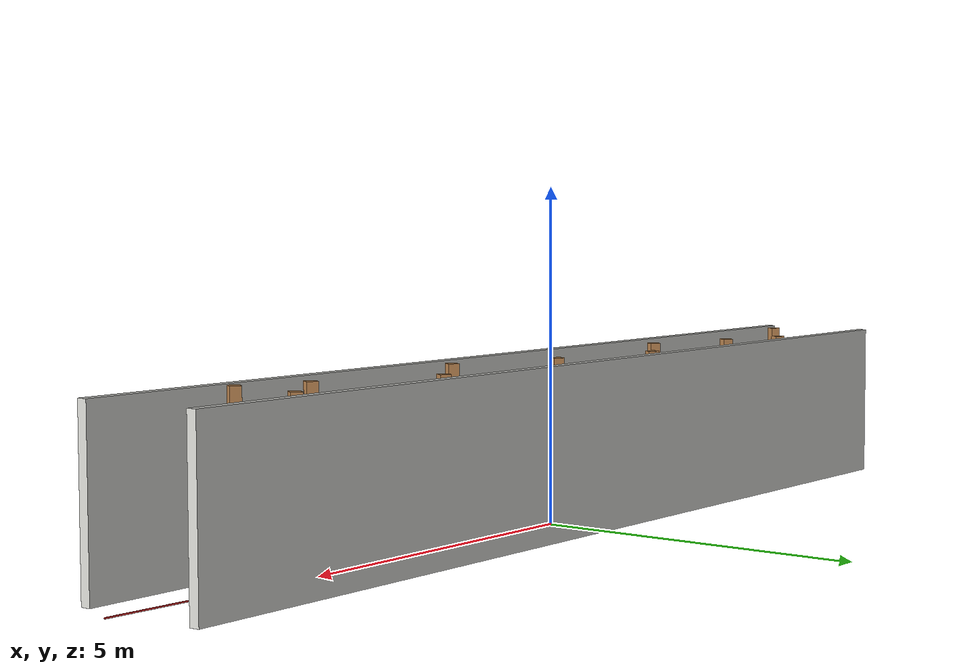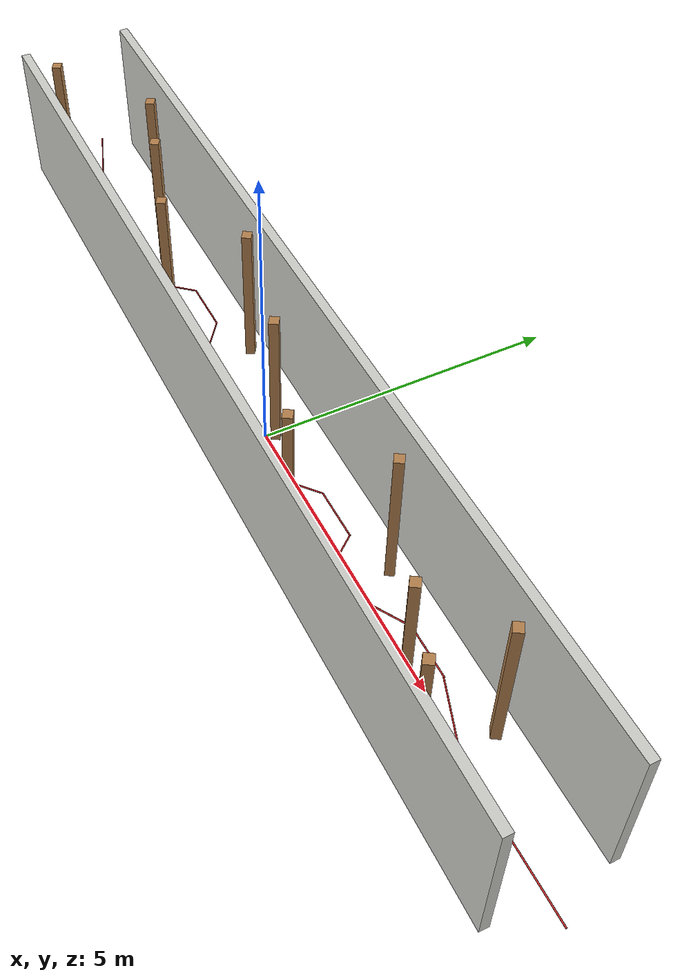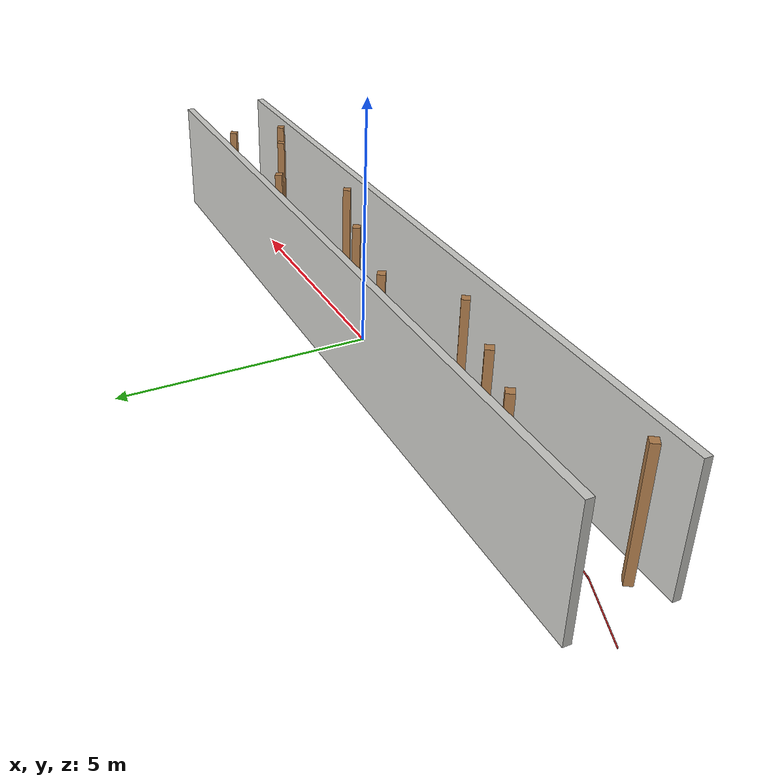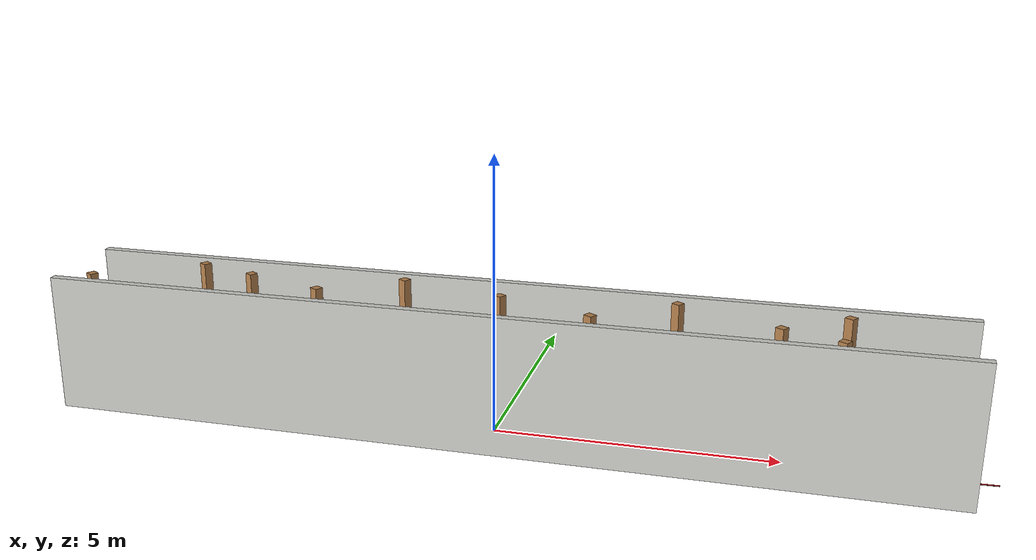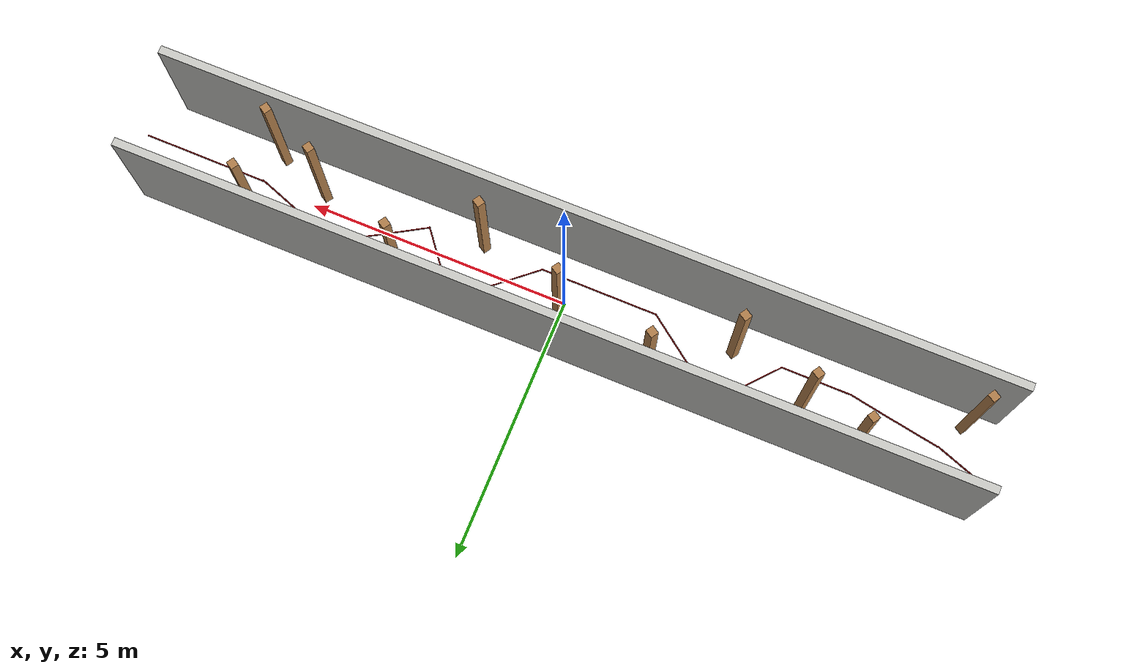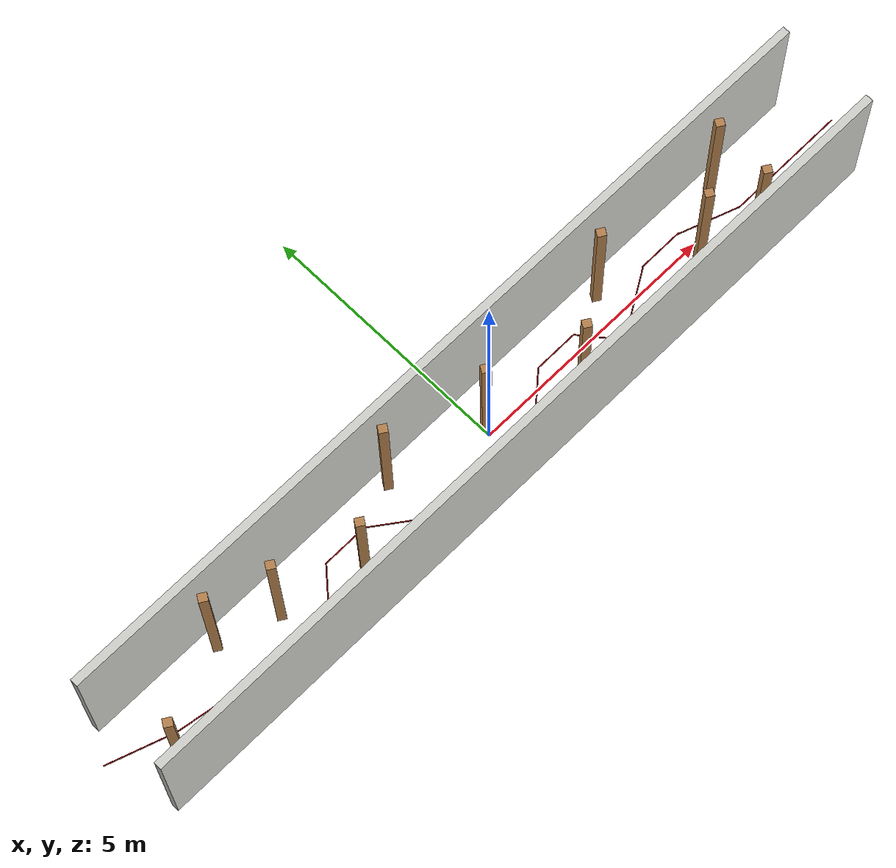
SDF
<?xml version='1.0'?>
<sdf version='1.6'>
  <model name='pole_2m_rope'>
    <link name='Wall_0'>
      <pose frame=''>-0.007783 0.925 0 0 -0 0</pose>
      <self_collide>0</self_collide>
      <enable_wind>0</enable_wind>
      <kinematic>0</kinematic>
      <inertial>
        <inertia>
          <ixx>0</ixx>
          <ixy>0</ixy>
          <ixz>0</ixz>
          <iyy>0</iyy>
          <iyz>0</iyz>
          <izz>0</izz>
        </inertia>
        <mass>0</mass>
        <pose frame=''>0 0 0 0 -0 0</pose>
      </inertial>
      <visual name='Wall_0_Visual'>
        <pose frame=''>0 0 1.25 0 -0 0</pose>
        <geometry>
          <box>
            <size>16.0312 0.15 2.5</size>
          </box>
        </geometry>
        <material>
          <script>
            <uri>file://media/materials/scripts/gazebo.material</uri>
            <name>Gazebo/CeilingTiled</name>
          </script>
          <ambient>1 1 1 1</ambient>
          <shader type='pixel'/>
        </material>
        <meta>
          <layer>0</layer>
        </meta>
        <transparency>0</transparency>
        <cast_shadows>1</cast_shadows>
      </visual>
      <collision name='Wall_0_Collision'>
        <laser_retro>0</laser_retro>
        <max_contacts>10</max_contacts>
        <pose frame=''>0 0 1.25 0 -0 0</pose>
        <geometry>
          <box>
            <size>16.0312 0.15 2.5</size>
          </box>
        </geometry>
        <surface>
          <friction>
            <ode>
              <mu>1</mu>
              <mu2>1</mu2>
              <fdir1>0 0 0</fdir1>
              <slip1>0</slip1>
              <slip2>0</slip2>
            </ode>
            <torsional>
              <coefficient>1</coefficient>
              <patch_radius>0</patch_radius>
              <surface_radius>0</surface_radius>
              <use_patch_radius>1</use_patch_radius>
              <ode>
                <slip>0</slip>
              </ode>
            </torsional>
          </friction>
          <bounce>
            <restitution_coefficient>0</restitution_coefficient>
            <threshold>1e+06</threshold>
          </bounce>
          <contact>
            <collide_without_contact>0</collide_without_contact>
            <collide_without_contact_bitmask>1</collide_without_contact_bitmask>
            <collide_bitmask>1</collide_bitmask>
            <ode>
              <soft_cfm>0</soft_cfm>
              <soft_erp>0.2</soft_erp>
              <kp>1e+13</kp>
              <kd>1</kd>
              <max_vel>0.01</max_vel>
              <min_depth>0</min_depth>
            </ode>
            <bullet>
              <split_impulse>1</split_impulse>
              <split_impulse_penetration_threshold>-0.01</split_impulse_penetration_threshold>
              <soft_cfm>0</soft_cfm>
              <soft_erp>0.2</soft_erp>
              <kp>1e+13</kp>
              <kd>1</kd>
            </bullet>
          </contact>
        </surface>
      </collision>
    </link>
    <link name='Wall_2'>
      <pose frame=''>0.006387 -0.928162 0 0 -0 3.14159</pose>
      <self_collide>0</self_collide>
      <enable_wind>0</enable_wind>
      <kinematic>0</kinematic>
      <inertial>
        <inertia>
          <ixx>0</ixx>
          <ixy>0</ixy>
          <ixz>0</ixz>
          <iyy>0</iyy>
          <iyz>0</iyz>
          <izz>0</izz>
        </inertia>
        <mass>0</mass>
        <pose frame=''>0 0 0 0 -0 0</pose>
      </inertial>
      <visual name='Wall_2_Visual'>
        <pose frame=''>0 0 1.25 0 -0 0</pose>
        <geometry>
          <box>
            <size>16.022 0.15 2.5</size>
          </box>
        </geometry>
        <material>
          <script>
            <uri>file://media/materials/scripts/gazebo.material</uri>
            <name>Gazebo/CeilingTiled</name>
          </script>
          <ambient>1 1 1 1</ambient>
          <shader type='pixel'/>
        </material>
        <meta>
          <layer>0</layer>
        </meta>
        <transparency>0</transparency>
        <cast_shadows>1</cast_shadows>
      </visual>
      <collision name='Wall_2_Collision'>
        <laser_retro>0</laser_retro>
        <max_contacts>10</max_contacts>
        <pose frame=''>0 0 1.25 0 -0 0</pose>
        <geometry>
          <box>
            <size>16.022 0.15 2.5</size>
          </box>
        </geometry>
        <surface>
          <friction>
            <ode>
              <mu>1</mu>
              <mu2>1</mu2>
              <fdir1>0 0 0</fdir1>
              <slip1>0</slip1>
              <slip2>0</slip2>
            </ode>
            <torsional>
              <coefficient>1</coefficient>
              <patch_radius>0</patch_radius>
              <surface_radius>0</surface_radius>
              <use_patch_radius>1</use_patch_radius>
              <ode>
                <slip>0</slip>
              </ode>
            </torsional>
          </friction>
          <bounce>
            <restitution_coefficient>0</restitution_coefficient>
            <threshold>1e+06</threshold>
          </bounce>
          <contact>
            <collide_without_contact>0</collide_without_contact>
            <collide_without_contact_bitmask>1</collide_without_contact_bitmask>
            <collide_bitmask>1</collide_bitmask>
            <ode>
              <soft_cfm>0</soft_cfm>
              <soft_erp>0.2</soft_erp>
              <kp>1e+13</kp>
              <kd>1</kd>
              <max_vel>0.01</max_vel>
              <min_depth>0</min_depth>
            </ode>
            <bullet>
              <split_impulse>1</split_impulse>
              <split_impulse_penetration_threshold>-0.01</split_impulse_penetration_threshold>
              <soft_cfm>0</soft_cfm>
              <soft_erp>0.2</soft_erp>
              <kp>1e+13</kp>
              <kd>1</kd>
            </bullet>
          </contact>
        </surface>
      </collision>
    </link>
    <link name='Wall_6'>
      <pose frame=''>-5.71878 0.5395 0 0 0 -0.558599</pose>
      <self_collide>0</self_collide>
      <enable_wind>0</enable_wind>
      <kinematic>0</kinematic>
      <visual name='Wall_6_Visual'>
        <pose frame=''>0 0 1.25 0 -0 0</pose>
        <geometry>
          <box>
            <size>0.16 0.15 2.5</size>
          </box>
        </geometry>
        <material>
          <script>
            <uri>file://media/materials/scripts/gazebo.material</uri>
            <name>Gazebo/Wood</name>
          </script>
          <ambient>1 1 1 1</ambient>
          <shader type='pixel'/>
        </material>
        <meta>
          <layer>0</layer>
        </meta>
        <transparency>0</transparency>
        <cast_shadows>1</cast_shadows>
      </visual>
      <collision name='Wall_6_Collision'>
        <laser_retro>0</laser_retro>
        <max_contacts>10</max_contacts>
        <pose frame=''>0 0 1.25 0 -0 0</pose>
        <geometry>
          <box>
            <size>0.16 0.15 2.5</size>
          </box>
        </geometry>
        <surface>
          <friction>
            <ode>
              <mu>1</mu>
              <mu2>1</mu2>
              <fdir1>0 0 0</fdir1>
              <slip1>0</slip1>
              <slip2>0</slip2>
            </ode>
            <torsional>
              <coefficient>1</coefficient>
              <patch_radius>0</patch_radius>
              <surface_radius>0</surface_radius>
              <use_patch_radius>1</use_patch_radius>
              <ode>
                <slip>0</slip>
              </ode>
            </torsional>
          </friction>
          <bounce>
            <restitution_coefficient>0</restitution_coefficient>
            <threshold>1e+06</threshold>
          </bounce>
          <contact>
            <collide_without_contact>0</collide_without_contact>
            <collide_without_contact_bitmask>1</collide_without_contact_bitmask>
            <collide_bitmask>1</collide_bitmask>
            <ode>
              <soft_cfm>0</soft_cfm>
              <soft_erp>0.2</soft_erp>
              <kp>1e+13</kp>
              <kd>1</kd>
              <max_vel>0.01</max_vel>
              <min_depth>0</min_depth>
            </ode>
            <bullet>
              <split_impulse>1</split_impulse>
              <split_impulse_penetration_threshold>-0.01</split_impulse_penetration_threshold>
              <soft_cfm>0</soft_cfm>
              <soft_erp>0.2</soft_erp>
              <kp>1e+13</kp>
              <kd>1</kd>
            </bullet>
          </contact>
        </surface>
      </collision>
    </link>
    <link name='Wall_6_clone'>
      <pose frame=''>-3.15849 -0.287445 0 0 0 -0.558599</pose>
      <self_collide>0</self_collide>
      <enable_wind>0</enable_wind>
      <kinematic>0</kinematic>
      <visual name='Wall_6_Visual'>
        <pose frame=''>0 0 1.25 0 -0 0</pose>
        <geometry>
          <box>
            <size>0.16 0.15 2.5</size>
          </box>
        </geometry>
        <material>
          <script>
            <uri>file://media/materials/scripts/gazebo.material</uri>
            <name>Gazebo/Wood</name>
          </script>
          <ambient>1 1 1 1</ambient>
          <shader type='pixel'/>
        </material>
        <meta>
          <layer>0</layer>
        </meta>
        <transparency>0</transparency>
        <cast_shadows>1</cast_shadows>
      </visual>
      <collision name='Wall_6_Collision'>
        <laser_retro>0</laser_retro>
        <max_contacts>10</max_contacts>
        <pose frame=''>0 0 1.25 0 -0 0</pose>
        <geometry>
          <box>
            <size>0.16 0.15 2.5</size>
          </box>
        </geometry>
        <surface>
          <friction>
            <ode>
              <mu>1</mu>
              <mu2>1</mu2>
              <fdir1>0 0 0</fdir1>
              <slip1>0</slip1>
              <slip2>0</slip2>
            </ode>
            <torsional>
              <coefficient>1</coefficient>
              <patch_radius>0</patch_radius>
              <surface_radius>0</surface_radius>
              <use_patch_radius>1</use_patch_radius>
              <ode>
                <slip>0</slip>
              </ode>
            </torsional>
          </friction>
          <bounce>
            <restitution_coefficient>0</restitution_coefficient>
            <threshold>1e+06</threshold>
          </bounce>
          <contact>
            <collide_without_contact>0</collide_without_contact>
            <collide_without_contact_bitmask>1</collide_without_contact_bitmask>
            <collide_bitmask>1</collide_bitmask>
            <ode>
              <soft_cfm>0</soft_cfm>
              <soft_erp>0.2</soft_erp>
              <kp>1e+13</kp>
              <kd>1</kd>
              <max_vel>0.01</max_vel>
              <min_depth>0</min_depth>
            </ode>
            <bullet>
              <split_impulse>1</split_impulse>
              <split_impulse_penetration_threshold>-0.01</split_impulse_penetration_threshold>
              <soft_cfm>0</soft_cfm>
              <soft_erp>0.2</soft_erp>
              <kp>1e+13</kp>
              <kd>1</kd>
            </bullet>
          </contact>
        </surface>
      </collision>
    </link>
    <link name='Wall_6_clone_0'>
      <pose frame=''>-1.81482 0.574676 0 0 0 -0.558599</pose>
      <self_collide>0</self_collide>
      <enable_wind>0</enable_wind>
      <kinematic>0</kinematic>
      <visual name='Wall_6_Visual'>
        <pose frame=''>0 0 1.25 0 -0 0</pose>
        <geometry>
          <box>
            <size>0.16 0.15 2.5</size>
          </box>
        </geometry>
        <material>
          <script>
            <uri>file://media/materials/scripts/gazebo.material</uri>
            <name>Gazebo/Wood</name>
          </script>
          <ambient>1 1 1 1</ambient>
          <shader type='pixel'/>
        </material>
        <meta>
          <layer>0</layer>
        </meta>
        <transparency>0</transparency>
        <cast_shadows>1</cast_shadows>
      </visual>
      <collision name='Wall_6_Collision'>
        <laser_retro>0</laser_retro>
        <max_contacts>10</max_contacts>
        <pose frame=''>0 0 1.25 0 -0 0</pose>
        <geometry>
          <box>
            <size>0.16 0.15 2.5</size>
          </box>
        </geometry>
        <surface>
          <friction>
            <ode>
              <mu>1</mu>
              <mu2>1</mu2>
              <fdir1>0 0 0</fdir1>
              <slip1>0</slip1>
              <slip2>0</slip2>
            </ode>
            <torsional>
              <coefficient>1</coefficient>
              <patch_radius>0</patch_radius>
              <surface_radius>0</surface_radius>
              <use_patch_radius>1</use_patch_radius>
              <ode>
                <slip>0</slip>
              </ode>
            </torsional>
          </friction>
          <bounce>
            <restitution_coefficient>0</restitution_coefficient>
            <threshold>1e+06</threshold>
          </bounce>
          <contact>
            <collide_without_contact>0</collide_without_contact>
            <collide_without_contact_bitmask>1</collide_without_contact_bitmask>
            <collide_bitmask>1</collide_bitmask>
            <ode>
              <soft_cfm>0</soft_cfm>
              <soft_erp>0.2</soft_erp>
              <kp>1e+13</kp>
              <kd>1</kd>
              <max_vel>0.01</max_vel>
              <min_depth>0</min_depth>
            </ode>
            <bullet>
              <split_impulse>1</split_impulse>
              <split_impulse_penetration_threshold>-0.01</split_impulse_penetration_threshold>
              <soft_cfm>0</soft_cfm>
              <soft_erp>0.2</soft_erp>
              <kp>1e+13</kp>
              <kd>1</kd>
            </bullet>
          </contact>
        </surface>
      </collision>
    </link>
    <link name='Wall_6_clone_1'>
      <pose frame=''>0.060149 0.149503 0 0 0 -0.558599</pose>
      <self_collide>0</self_collide>
      <enable_wind>0</enable_wind>
      <kinematic>0</kinematic>
      <visual name='Wall_6_Visual'>
        <pose frame=''>0 0 1.25 0 -0 0</pose>
        <geometry>
          <box>
            <size>0.16 0.15 2.5</size>
          </box>
        </geometry>
        <material>
          <script>
            <uri>file://media/materials/scripts/gazebo.material</uri>
            <name>Gazebo/Wood</name>
          </script>
          <ambient>1 1 1 1</ambient>
          <shader type='pixel'/>
        </material>
        <meta>
          <layer>0</layer>
        </meta>
        <transparency>0</transparency>
        <cast_shadows>1</cast_shadows>
      </visual>
      <collision name='Wall_6_Collision'>
        <laser_retro>0</laser_retro>
        <max_contacts>10</max_contacts>
        <pose frame=''>0 0 1.25 0 -0 0</pose>
        <geometry>
          <box>
            <size>0.16 0.15 2.5</size>
          </box>
        </geometry>
        <surface>
          <friction>
            <ode>
              <mu>1</mu>
              <mu2>1</mu2>
              <fdir1>0 0 0</fdir1>
              <slip1>0</slip1>
              <slip2>0</slip2>
            </ode>
            <torsional>
              <coefficient>1</coefficient>
              <patch_radius>0</patch_radius>
              <surface_radius>0</surface_radius>
              <use_patch_radius>1</use_patch_radius>
              <ode>
                <slip>0</slip>
              </ode>
            </torsional>
          </friction>
          <bounce>
            <restitution_coefficient>0</restitution_coefficient>
            <threshold>1e+06</threshold>
          </bounce>
          <contact>
            <collide_without_contact>0</collide_without_contact>
            <collide_without_contact_bitmask>1</collide_without_contact_bitmask>
            <collide_bitmask>1</collide_bitmask>
            <ode>
              <soft_cfm>0</soft_cfm>
              <soft_erp>0.2</soft_erp>
              <kp>1e+13</kp>
              <kd>1</kd>
              <max_vel>0.01</max_vel>
              <min_depth>0</min_depth>
            </ode>
            <bullet>
              <split_impulse>1</split_impulse>
              <split_impulse_penetration_threshold>-0.01</split_impulse_penetration_threshold>
              <soft_cfm>0</soft_cfm>
              <soft_erp>0.2</soft_erp>
              <kp>1e+13</kp>
              <kd>1</kd>
            </bullet>
          </contact>
        </surface>
      </collision>
    </link>
    <link name='Wall_6_clone_2'>
      <pose frame=''>1.75896 -0.448581 0 0 0 -0.558599</pose>
      <self_collide>0</self_collide>
      <enable_wind>0</enable_wind>
      <kinematic>0</kinematic>
      <visual name='Wall_6_Visual'>
        <pose frame=''>0 0 1.25 0 -0 0</pose>
        <geometry>
          <box>
            <size>0.16 0.15 2.5</size>
          </box>
        </geometry>
        <material>
          <script>
            <uri>file://media/materials/scripts/gazebo.material</uri>
            <name>Gazebo/Wood</name>
          </script>
          <ambient>1 1 1 1</ambient>
          <shader type='pixel'/>
        </material>
        <meta>
          <layer>0</layer>
        </meta>
        <transparency>0</transparency>
        <cast_shadows>1</cast_shadows>
      </visual>
      <collision name='Wall_6_Collision'>
        <laser_retro>0</laser_retro>
        <max_contacts>10</max_contacts>
        <pose frame=''>0 0 1.25 0 -0 0</pose>
        <geometry>
          <box>
            <size>0.16 0.15 2.5</size>
          </box>
        </geometry>
        <surface>
          <friction>
            <ode>
              <mu>1</mu>
              <mu2>1</mu2>
              <fdir1>0 0 0</fdir1>
              <slip1>0</slip1>
              <slip2>0</slip2>
            </ode>
            <torsional>
              <coefficient>1</coefficient>
              <patch_radius>0</patch_radius>
              <surface_radius>0</surface_radius>
              <use_patch_radius>1</use_patch_radius>
              <ode>
                <slip>0</slip>
              </ode>
            </torsional>
          </friction>
          <bounce>
            <restitution_coefficient>0</restitution_coefficient>
            <threshold>1e+06</threshold>
          </bounce>
          <contact>
            <collide_without_contact>0</collide_without_contact>
            <collide_without_contact_bitmask>1</collide_without_contact_bitmask>
            <collide_bitmask>1</collide_bitmask>
            <ode>
              <soft_cfm>0</soft_cfm>
              <soft_erp>0.2</soft_erp>
              <kp>1e+13</kp>
              <kd>1</kd>
              <max_vel>0.01</max_vel>
              <min_depth>0</min_depth>
            </ode>
            <bullet>
              <split_impulse>1</split_impulse>
              <split_impulse_penetration_threshold>-0.01</split_impulse_penetration_threshold>
              <soft_cfm>0</soft_cfm>
              <soft_erp>0.2</soft_erp>
              <kp>1e+13</kp>
              <kd>1</kd>
            </bullet>
          </contact>
        </surface>
      </collision>
    </link>
    <link name='Wall_6_clone_3'>
      <pose frame=''>3.08943 0.513137 0 0 0 -0.558599</pose>
      <self_collide>0</self_collide>
      <enable_wind>0</enable_wind>
      <kinematic>0</kinematic>
      <visual name='Wall_6_Visual'>
        <pose frame=''>0 0 1.25 0 -0 0</pose>
        <geometry>
          <box>
            <size>0.16 0.15 2.5</size>
          </box>
        </geometry>
        <material>
          <script>
            <uri>file://media/materials/scripts/gazebo.material</uri>
            <name>Gazebo/Wood</name>
          </script>
          <ambient>1 1 1 1</ambient>
          <shader type='pixel'/>
        </material>
        <meta>
          <layer>0</layer>
        </meta>
        <transparency>0</transparency>
        <cast_shadows>1</cast_shadows>
      </visual>
      <collision name='Wall_6_Collision'>
        <laser_retro>0</laser_retro>
        <max_contacts>10</max_contacts>
        <pose frame=''>0 0 1.25 0 -0 0</pose>
        <geometry>
          <box>
            <size>0.16 0.15 2.5</size>
          </box>
        </geometry>
        <surface>
          <friction>
            <ode>
              <mu>1</mu>
              <mu2>1</mu2>
              <fdir1>0 0 0</fdir1>
              <slip1>0</slip1>
              <slip2>0</slip2>
            </ode>
            <torsional>
              <coefficient>1</coefficient>
              <patch_radius>0</patch_radius>
              <surface_radius>0</surface_radius>
              <use_patch_radius>1</use_patch_radius>
              <ode>
                <slip>0</slip>
              </ode>
            </torsional>
          </friction>
          <bounce>
            <restitution_coefficient>0</restitution_coefficient>
            <threshold>1e+06</threshold>
          </bounce>
          <contact>
            <collide_without_contact>0</collide_without_contact>
            <collide_without_contact_bitmask>1</collide_without_contact_bitmask>
            <collide_bitmask>1</collide_bitmask>
            <ode>
              <soft_cfm>0</soft_cfm>
              <soft_erp>0.2</soft_erp>
              <kp>1e+13</kp>
              <kd>1</kd>
              <max_vel>0.01</max_vel>
              <min_depth>0</min_depth>
            </ode>
            <bullet>
              <split_impulse>1</split_impulse>
              <split_impulse_penetration_threshold>-0.01</split_impulse_penetration_threshold>
              <soft_cfm>0</soft_cfm>
              <soft_erp>0.2</soft_erp>
              <kp>1e+13</kp>
              <kd>1</kd>
            </bullet>
          </contact>
        </surface>
      </collision>
    </link>
    <link name='Wall_6_clone_4'>
      <pose frame=''>4.85406 -0.243061 0 0 0 -0.558599</pose>
      <self_collide>0</self_collide>
      <enable_wind>0</enable_wind>
      <kinematic>0</kinematic>
      <visual name='Wall_6_Visual'>
        <pose frame=''>0 0 1.25 0 -0 0</pose>
        <geometry>
          <box>
            <size>0.16 0.15 2.5</size>
          </box>
        </geometry>
        <material>
          <script>
            <uri>file://media/materials/scripts/gazebo.material</uri>
            <name>Gazebo/Wood</name>
          </script>
          <ambient>1 1 1 1</ambient>
          <shader type='pixel'/>
        </material>
        <meta>
          <layer>0</layer>
        </meta>
        <transparency>0</transparency>
        <cast_shadows>1</cast_shadows>
      </visual>
      <collision name='Wall_6_Collision'>
        <laser_retro>0</laser_retro>
        <max_contacts>10</max_contacts>
        <pose frame=''>0 0 1.25 0 -0 0</pose>
        <geometry>
          <box>
            <size>0.16 0.15 2.5</size>
          </box>
        </geometry>
        <surface>
          <friction>
            <ode>
              <mu>1</mu>
              <mu2>1</mu2>
              <fdir1>0 0 0</fdir1>
              <slip1>0</slip1>
              <slip2>0</slip2>
            </ode>
            <torsional>
              <coefficient>1</coefficient>
              <patch_radius>0</patch_radius>
              <surface_radius>0</surface_radius>
              <use_patch_radius>1</use_patch_radius>
              <ode>
                <slip>0</slip>
              </ode>
            </torsional>
          </friction>
          <bounce>
            <restitution_coefficient>0</restitution_coefficient>
            <threshold>1e+06</threshold>
          </bounce>
          <contact>
            <collide_without_contact>0</collide_without_contact>
            <collide_without_contact_bitmask>1</collide_without_contact_bitmask>
            <collide_bitmask>1</collide_bitmask>
            <ode>
              <soft_cfm>0</soft_cfm>
              <soft_erp>0.2</soft_erp>
              <kp>1e+13</kp>
              <kd>1</kd>
              <max_vel>0.01</max_vel>
              <min_depth>0</min_depth>
            </ode>
            <bullet>
              <split_impulse>1</split_impulse>
              <split_impulse_penetration_threshold>-0.01</split_impulse_penetration_threshold>
              <soft_cfm>0</soft_cfm>
              <soft_erp>0.2</soft_erp>
              <kp>1e+13</kp>
              <kd>1</kd>
            </bullet>
          </contact>
        </surface>
      </collision>
    </link>
    <link name='Wall_6_clone_5'>
      <pose frame=''>5.92825 0.520399 0 0 0 -0.558599</pose>
      <self_collide>0</self_collide>
      <enable_wind>0</enable_wind>
      <kinematic>0</kinematic>
      <visual name='Wall_6_Visual'>
        <pose frame=''>0 0 1.25 0 -0 0</pose>
        <geometry>
          <box>
            <size>0.16 0.15 2.5</size>
          </box>
        </geometry>
        <material>
          <script>
            <uri>file://media/materials/scripts/gazebo.material</uri>
            <name>Gazebo/Wood</name>
          </script>
          <ambient>1 1 1 1</ambient>
          <shader type='pixel'/>
        </material>
        <meta>
          <layer>0</layer>
        </meta>
        <transparency>0</transparency>
        <cast_shadows>1</cast_shadows>
      </visual>
      <collision name='Wall_6_Collision'>
        <laser_retro>0</laser_retro>
        <max_contacts>10</max_contacts>
        <pose frame=''>0 0 1.25 0 -0 0</pose>
        <geometry>
          <box>
            <size>0.16 0.15 2.5</size>
          </box>
        </geometry>
        <surface>
          <friction>
            <ode>
              <mu>1</mu>
              <mu2>1</mu2>
              <fdir1>0 0 0</fdir1>
              <slip1>0</slip1>
              <slip2>0</slip2>
            </ode>
            <torsional>
              <coefficient>1</coefficient>
              <patch_radius>0</patch_radius>
              <surface_radius>0</surface_radius>
              <use_patch_radius>1</use_patch_radius>
              <ode>
                <slip>0</slip>
              </ode>
            </torsional>
          </friction>
          <bounce>
            <restitution_coefficient>0</restitution_coefficient>
            <threshold>1e+06</threshold>
          </bounce>
          <contact>
            <collide_without_contact>0</collide_without_contact>
            <collide_without_contact_bitmask>1</collide_without_contact_bitmask>
            <collide_bitmask>1</collide_bitmask>
            <ode>
              <soft_cfm>0</soft_cfm>
              <soft_erp>0.2</soft_erp>
              <kp>1e+13</kp>
              <kd>1</kd>
              <max_vel>0.01</max_vel>
              <min_depth>0</min_depth>
            </ode>
            <bullet>
              <split_impulse>1</split_impulse>
              <split_impulse_penetration_threshold>-0.01</split_impulse_penetration_threshold>
              <soft_cfm>0</soft_cfm>
              <soft_erp>0.2</soft_erp>
              <kp>1e+13</kp>
              <kd>1</kd>
            </bullet>
          </contact>
        </surface>
      </collision>
    </link>
    <link name='Wall_6_clone_6'>
      <pose frame=''>-7.43919 -0.539254 0 0 0 -0.558599</pose>
      <self_collide>0</self_collide>
      <enable_wind>0</enable_wind>
      <kinematic>0</kinematic>
      <visual name='Wall_6_Visual'>
        <pose frame=''>0 0 1.25 0 -0 0</pose>
        <geometry>
          <box>
            <size>0.16 0.15 2.5</size>
          </box>
        </geometry>
        <material>
          <script>
            <uri>file://media/materials/scripts/gazebo.material</uri>
            <name>Gazebo/Wood</name>
          </script>
          <ambient>1 1 1 1</ambient>
          <shader type='pixel'/>
        </material>
        <meta>
          <layer>0</layer>
        </meta>
        <transparency>0</transparency>
        <cast_shadows>1</cast_shadows>
      </visual>
      <collision name='Wall_6_Collision'>
        <laser_retro>0</laser_retro>
        <max_contacts>10</max_contacts>
        <pose frame=''>0 0 1.25 0 -0 0</pose>
        <geometry>
          <box>
            <size>0.16 0.15 2.5</size>
          </box>
        </geometry>
        <surface>
          <friction>
            <ode>
              <mu>1</mu>
              <mu2>1</mu2>
              <fdir1>0 0 0</fdir1>
              <slip1>0</slip1>
              <slip2>0</slip2>
            </ode>
            <torsional>
              <coefficient>1</coefficient>
              <patch_radius>0</patch_radius>
              <surface_radius>0</surface_radius>
              <use_patch_radius>1</use_patch_radius>
              <ode>
                <slip>0</slip>
              </ode>
            </torsional>
          </friction>
          <bounce>
            <restitution_coefficient>0</restitution_coefficient>
            <threshold>1e+06</threshold>
          </bounce>
          <contact>
            <collide_without_contact>0</collide_without_contact>
            <collide_without_contact_bitmask>1</collide_without_contact_bitmask>
            <collide_bitmask>1</collide_bitmask>
            <ode>
              <soft_cfm>0</soft_cfm>
              <soft_erp>0.2</soft_erp>
              <kp>1e+13</kp>
              <kd>1</kd>
              <max_vel>0.01</max_vel>
              <min_depth>0</min_depth>
            </ode>
            <bullet>
              <split_impulse>1</split_impulse>
              <split_impulse_penetration_threshold>-0.01</split_impulse_penetration_threshold>
              <soft_cfm>0</soft_cfm>
              <soft_erp>0.2</soft_erp>
              <kp>1e+13</kp>
              <kd>1</kd>
            </bullet>
          </contact>
        </surface>
      </collision>
    </link>
    <link name='Wall_6_clone_7'>
      <pose frame=''>5.84024 -0.624639 0 0 0 -0.558599</pose>
      <self_collide>0</self_collide>
      <enable_wind>0</enable_wind>
      <kinematic>0</kinematic>
      <visual name='Wall_6_Visual'>
        <pose frame=''>0 0 1.25 0 -0 0</pose>
        <geometry>
          <box>
            <size>0.16 0.15 2.5</size>
          </box>
        </geometry>
        <material>
          <script>
            <uri>file://media/materials/scripts/gazebo.material</uri>
            <name>Gazebo/Wood</name>
          </script>
          <ambient>1 1 1 1</ambient>
          <shader type='pixel'/>
        </material>
        <meta>
          <layer>0</layer>
        </meta>
        <transparency>0</transparency>
        <cast_shadows>1</cast_shadows>
      </visual>
      <collision name='Wall_6_Collision'>
        <laser_retro>0</laser_retro>
        <max_contacts>10</max_contacts>
        <pose frame=''>0 0 1.25 0 -0 0</pose>
        <geometry>
          <box>
            <size>0.16 0.15 2.5</size>
          </box>
        </geometry>
        <surface>
          <friction>
            <ode>
              <mu>1</mu>
              <mu2>1</mu2>
              <fdir1>0 0 0</fdir1>
              <slip1>0</slip1>
              <slip2>0</slip2>
            </ode>
            <torsional>
              <coefficient>1</coefficient>
              <patch_radius>0</patch_radius>
              <surface_radius>0</surface_radius>
              <use_patch_radius>1</use_patch_radius>
              <ode>
                <slip>0</slip>
              </ode>
            </torsional>
          </friction>
          <bounce>
            <restitution_coefficient>0</restitution_coefficient>
            <threshold>1e+06</threshold>
          </bounce>
          <contact>
            <collide_without_contact>0</collide_without_contact>
            <collide_without_contact_bitmask>1</collide_without_contact_bitmask>
            <collide_bitmask>1</collide_bitmask>
            <ode>
              <soft_cfm>0</soft_cfm>
              <soft_erp>0.2</soft_erp>
              <kp>1e+13</kp>
              <kd>1</kd>
              <max_vel>0.01</max_vel>
              <min_depth>0</min_depth>
            </ode>
            <bullet>
              <split_impulse>1</split_impulse>
              <split_impulse_penetration_threshold>-0.01</split_impulse_penetration_threshold>
              <soft_cfm>0</soft_cfm>
              <soft_erp>0.2</soft_erp>
              <kp>1e+13</kp>
              <kd>1</kd>
            </bullet>
          </contact>
        </surface>
      </collision>
    </link>
    <link name='Wall_6_clone_8'>
      <pose frame=''>-4.62403 0.184371 0 0 0 -0.558599</pose>
      <self_collide>0</self_collide>
      <enable_wind>0</enable_wind>
      <kinematic>0</kinematic>
      <visual name='Wall_6_Visual'>
        <pose frame=''>0 0 1.25 0 -0 0</pose>
        <geometry>
          <box>
            <size>0.16 0.15 2.5</size>
          </box>
        </geometry>
        <material>
          <script>
            <uri>file://media/materials/scripts/gazebo.material</uri>
            <name>Gazebo/Wood</name>
          </script>
          <ambient>1 1 1 1</ambient>
          <shader type='pixel'/>
        </material>
        <meta>
          <layer>0</layer>
        </meta>
        <transparency>0</transparency>
        <cast_shadows>1</cast_shadows>
      </visual>
      <collision name='Wall_6_Collision'>
        <laser_retro>0</laser_retro>
        <max_contacts>10</max_contacts>
        <pose frame=''>0 0 1.25 0 -0 0</pose>
        <geometry>
          <box>
            <size>0.16 0.15 2.5</size>
          </box>
        </geometry>
        <surface>
          <friction>
            <ode>
              <mu>1</mu>
              <mu2>1</mu2>
              <fdir1>0 0 0</fdir1>
              <slip1>0</slip1>
              <slip2>0</slip2>
            </ode>
            <torsional>
              <coefficient>1</coefficient>
              <patch_radius>0</patch_radius>
              <surface_radius>0</surface_radius>
              <use_patch_radius>1</use_patch_radius>
              <ode>
                <slip>0</slip>
              </ode>
            </torsional>
          </friction>
          <bounce>
            <restitution_coefficient>0</restitution_coefficient>
            <threshold>1e+06</threshold>
          </bounce>
          <contact>
            <collide_without_contact>0</collide_without_contact>
            <collide_without_contact_bitmask>1</collide_without_contact_bitmask>
            <collide_bitmask>1</collide_bitmask>
            <ode>
              <soft_cfm>0</soft_cfm>
              <soft_erp>0.2</soft_erp>
              <kp>1e+13</kp>
              <kd>1</kd>
              <max_vel>0.01</max_vel>
              <min_depth>0</min_depth>
            </ode>
            <bullet>
              <split_impulse>1</split_impulse>
              <split_impulse_penetration_threshold>-0.01</split_impulse_penetration_threshold>
              <soft_cfm>0</soft_cfm>
              <soft_erp>0.2</soft_erp>
              <kp>1e+13</kp>
              <kd>1</kd>
            </bullet>
          </contact>
        </surface>
      </collision>
    </link>
    <link name='link_4'>
      <inertial>
        <mass>0.00045611</mass>
        <inertia>
          <ixx>3.061e-05</ixx>
          <ixy>0</ixy>
          <ixz>0</ixz>
          <iyy>3.061e-05</iyy>
          <iyz>0</iyz>
          <izz>3e-08</izz>
        </inertia>
        <pose frame=''>0 0 0 0 -0 0</pose>
      </inertial>
      <pose frame=''>-6.72603 -0.128622 0.047823 2.97338 -1.55695 3.14159</pose>
      <gravity>1</gravity>
      <self_collide>0</self_collide>
      <kinematic>0</kinematic>
      <enable_wind>0</enable_wind>
      <visual name='visual'>
        <pose frame=''>0 0 0 0 -0 0</pose>
        <geometry>
          <cylinder>
            <radius>0.0113187</radius>
            <length>0.897241</length>
          </cylinder>
        </geometry>
        <material>
          <lighting>1</lighting>
          <script>
            <uri>file://media/materials/scripts/gazebo.material</uri>
            <name>Gazebo/Red</name>
          </script>
          <shader type='pixel'>
            <normal_map>__default__</normal_map>
          </shader>
          <ambient>1 0 0 1</ambient>
          <diffuse>1 0 0 1</diffuse>
          <specular>0.1 0.1 0.1 1</specular>
          <emissive>0 0 0 1</emissive>
        </material>
        <transparency>0</transparency>
        <cast_shadows>1</cast_shadows>
      </visual>
      <collision name='collision'>
        <laser_retro>0</laser_retro>
        <max_contacts>10</max_contacts>
        <pose frame=''>0 0 0 0 -0 0</pose>
        <geometry>
          <cylinder>
            <radius>0.011319</radius>
            <length>0.897241</length>
          </cylinder>
        </geometry>
        <surface>
          <friction>
            <ode>
              <mu>1</mu>
              <mu2>1</mu2>
              <fdir1>0 0 0</fdir1>
              <slip1>0</slip1>
              <slip2>0</slip2>
            </ode>
            <torsional>
              <coefficient>1</coefficient>
              <patch_radius>0</patch_radius>
              <surface_radius>0</surface_radius>
              <use_patch_radius>1</use_patch_radius>
              <ode>
                <slip>0</slip>
              </ode>
            </torsional>
          </friction>
          <bounce>
            <restitution_coefficient>0</restitution_coefficient>
            <threshold>1e+06</threshold>
          </bounce>
          <contact>
            <collide_without_contact>0</collide_without_contact>
            <collide_without_contact_bitmask>1</collide_without_contact_bitmask>
            <collide_bitmask>1</collide_bitmask>
            <ode>
              <soft_cfm>0</soft_cfm>
              <soft_erp>0.2</soft_erp>
              <kp>1e+13</kp>
              <kd>1</kd>
              <max_vel>0.01</max_vel>
              <min_depth>0</min_depth>
            </ode>
            <bullet>
              <split_impulse>1</split_impulse>
              <split_impulse_penetration_threshold>-0.01</split_impulse_penetration_threshold>
              <soft_cfm>0</soft_cfm>
              <soft_erp>0.2</soft_erp>
              <kp>1e+13</kp>
              <kd>1</kd>
            </bullet>
          </contact>
        </surface>
      </collision>
    </link>
    <link name='link_4_clone'>
      <inertial>
        <mass>0.00045611</mass>
        <inertia>
          <ixx>3.061e-05</ixx>
          <ixy>0</ixy>
          <ixz>0</ixz>
          <iyy>3.061e-05</iyy>
          <iyz>0</iyz>
          <izz>3e-08</izz>
        </inertia>
        <pose frame=''>0 0 0 0 -0 0</pose>
      </inertial>
      <pose frame=''>-5.84641 -0.284258 0.047823 2.96308 -1.55695 3.14159</pose>
      <gravity>1</gravity>
      <self_collide>0</self_collide>
      <kinematic>0</kinematic>
      <enable_wind>0</enable_wind>
      <visual name='visual'>
        <pose frame=''>0 0 0 0 -0 0</pose>
        <geometry>
          <cylinder>
            <radius>0.0113187</radius>
            <length>0.897241</length>
          </cylinder>
        </geometry>
        <material>
          <lighting>1</lighting>
          <script>
            <uri>file://media/materials/scripts/gazebo.material</uri>
            <name>Gazebo/Red</name>
          </script>
          <shader type='pixel'>
            <normal_map>__default__</normal_map>
          </shader>
          <ambient>1 0 0 1</ambient>
          <diffuse>1 0 0 1</diffuse>
          <specular>0.1 0.1 0.1 1</specular>
          <emissive>0 0 0 1</emissive>
        </material>
        <transparency>0</transparency>
        <cast_shadows>1</cast_shadows>
      </visual>
      <collision name='collision'>
        <laser_retro>0</laser_retro>
        <max_contacts>10</max_contacts>
        <pose frame=''>0 0 0 0 -0 0</pose>
        <geometry>
          <cylinder>
            <radius>0.011319</radius>
            <length>0.897241</length>
          </cylinder>
        </geometry>
        <surface>
          <friction>
            <ode>
              <mu>1</mu>
              <mu2>1</mu2>
              <fdir1>0 0 0</fdir1>
              <slip1>0</slip1>
              <slip2>0</slip2>
            </ode>
            <torsional>
              <coefficient>1</coefficient>
              <patch_radius>0</patch_radius>
              <surface_radius>0</surface_radius>
              <use_patch_radius>1</use_patch_radius>
              <ode>
                <slip>0</slip>
              </ode>
            </torsional>
          </friction>
          <bounce>
            <restitution_coefficient>0</restitution_coefficient>
            <threshold>1e+06</threshold>
          </bounce>
          <contact>
            <collide_without_contact>0</collide_without_contact>
            <collide_without_contact_bitmask>1</collide_without_contact_bitmask>
            <collide_bitmask>1</collide_bitmask>
            <ode>
              <soft_cfm>0</soft_cfm>
              <soft_erp>0.2</soft_erp>
              <kp>1e+13</kp>
              <kd>1</kd>
              <max_vel>0.01</max_vel>
              <min_depth>0</min_depth>
            </ode>
            <bullet>
              <split_impulse>1</split_impulse>
              <split_impulse_penetration_threshold>-0.01</split_impulse_penetration_threshold>
              <soft_cfm>0</soft_cfm>
              <soft_erp>0.2</soft_erp>
              <kp>1e+13</kp>
              <kd>1</kd>
            </bullet>
          </contact>
        </surface>
      </collision>
    </link>
    <link name='link_4_clone_0'>
      <inertial>
        <mass>0.000680335</mass>
        <inertia>
          <ixx>0.000103691</ixx>
          <ixy>0</ixy>
          <ixz>0</ixz>
          <iyy>0.000103691</iyy>
          <iyz>0</iyz>
          <izz>4.35799e-08</izz>
        </inertia>
        <pose frame=''>0 0 0 0 -0 0</pose>
      </inertial>
      <pose frame=''>-4.74113 -0.367074 0.047823 3.14159 -1.55695 3.14159</pose>
      <gravity>1</gravity>
      <self_collide>0</self_collide>
      <kinematic>0</kinematic>
      <enable_wind>0</enable_wind>
      <visual name='visual'>
        <pose frame=''>0 0 0 0 -0 0</pose>
        <geometry>
          <cylinder>
            <radius>0.0113187</radius>
            <length>1.35224</length>
          </cylinder>
        </geometry>
        <material>
          <lighting>1</lighting>
          <script>
            <uri>file://media/materials/scripts/gazebo.material</uri>
            <name>Gazebo/Red</name>
          </script>
          <shader type='pixel'>
            <normal_map>__default__</normal_map>
          </shader>
          <ambient>1 0 0 1</ambient>
          <diffuse>1 0 0 1</diffuse>
          <specular>0.1 0.1 0.1 1</specular>
          <emissive>0 0 0 1</emissive>
        </material>
        <transparency>0</transparency>
        <cast_shadows>1</cast_shadows>
      </visual>
      <collision name='collision'>
        <laser_retro>0</laser_retro>
        <max_contacts>10</max_contacts>
        <pose frame=''>0 0 0 0 -0 0</pose>
        <geometry>
          <cylinder>
            <radius>0.011319</radius>
            <length>1.35224</length>
          </cylinder>
        </geometry>
        <surface>
          <friction>
            <ode>
              <mu>1</mu>
              <mu2>1</mu2>
              <fdir1>0 0 0</fdir1>
              <slip1>0</slip1>
              <slip2>0</slip2>
            </ode>
            <torsional>
              <coefficient>1</coefficient>
              <patch_radius>0</patch_radius>
              <surface_radius>0</surface_radius>
              <use_patch_radius>1</use_patch_radius>
              <ode>
                <slip>0</slip>
              </ode>
            </torsional>
          </friction>
          <bounce>
            <restitution_coefficient>0</restitution_coefficient>
            <threshold>1e+06</threshold>
          </bounce>
          <contact>
            <collide_without_contact>0</collide_without_contact>
            <collide_without_contact_bitmask>1</collide_without_contact_bitmask>
            <collide_bitmask>1</collide_bitmask>
            <ode>
              <soft_cfm>0</soft_cfm>
              <soft_erp>0.2</soft_erp>
              <kp>1e+13</kp>
              <kd>1</kd>
              <max_vel>0.01</max_vel>
              <min_depth>0</min_depth>
            </ode>
            <bullet>
              <split_impulse>1</split_impulse>
              <split_impulse_penetration_threshold>-0.01</split_impulse_penetration_threshold>
              <soft_cfm>0</soft_cfm>
              <soft_erp>0.2</soft_erp>
              <kp>1e+13</kp>
              <kd>1</kd>
            </bullet>
          </contact>
        </surface>
      </collision>
    </link>
    <link name='link_4_clone_1'>
      <inertial>
        <mass>0.00045611</mass>
        <inertia>
          <ixx>3.061e-05</ixx>
          <ixy>0</ixy>
          <ixz>0</ixz>
          <iyy>3.061e-05</iyy>
          <iyz>0</iyz>
          <izz>3e-08</izz>
        </inertia>
        <pose frame=''>0 0 0 0 -0 0</pose>
      </inertial>
      <pose frame=''>-3.06044 0.304417 0.047823 3.14159 -1.55695 3.14159</pose>
      <gravity>1</gravity>
      <self_collide>0</self_collide>
      <kinematic>0</kinematic>
      <enable_wind>0</enable_wind>
      <visual name='visual'>
        <pose frame=''>0 0 0 0 -0 0</pose>
        <geometry>
          <cylinder>
            <radius>0.0113187</radius>
            <length>0.897241</length>
          </cylinder>
        </geometry>
        <material>
          <lighting>1</lighting>
          <script>
            <uri>file://media/materials/scripts/gazebo.material</uri>
            <name>Gazebo/Red</name>
          </script>
          <shader type='pixel'>
            <normal_map>__default__</normal_map>
          </shader>
          <ambient>1 0 0 1</ambient>
          <diffuse>1 0 0 1</diffuse>
          <specular>0.1 0.1 0.1 1</specular>
          <emissive>0 0 0 1</emissive>
        </material>
        <transparency>0</transparency>
        <cast_shadows>1</cast_shadows>
      </visual>
      <collision name='collision'>
        <laser_retro>0</laser_retro>
        <max_contacts>10</max_contacts>
        <pose frame=''>0 0 0 0 -0 0</pose>
        <geometry>
          <cylinder>
            <radius>0.011319</radius>
            <length>0.897241</length>
          </cylinder>
        </geometry>
        <surface>
          <friction>
            <ode>
              <mu>1</mu>
              <mu2>1</mu2>
              <fdir1>0 0 0</fdir1>
              <slip1>0</slip1>
              <slip2>0</slip2>
            </ode>
            <torsional>
              <coefficient>1</coefficient>
              <patch_radius>0</patch_radius>
              <surface_radius>0</surface_radius>
              <use_patch_radius>1</use_patch_radius>
              <ode>
                <slip>0</slip>
              </ode>
            </torsional>
          </friction>
          <bounce>
            <restitution_coefficient>0</restitution_coefficient>
            <threshold>1e+06</threshold>
          </bounce>
          <contact>
            <collide_without_contact>0</collide_without_contact>
            <collide_without_contact_bitmask>1</collide_without_contact_bitmask>
            <collide_bitmask>1</collide_bitmask>
            <ode>
              <soft_cfm>0</soft_cfm>
              <soft_erp>0.2</soft_erp>
              <kp>1e+13</kp>
              <kd>1</kd>
              <max_vel>0.01</max_vel>
              <min_depth>0</min_depth>
            </ode>
            <bullet>
              <split_impulse>1</split_impulse>
              <split_impulse_penetration_threshold>-0.01</split_impulse_penetration_threshold>
              <soft_cfm>0</soft_cfm>
              <soft_erp>0.2</soft_erp>
              <kp>1e+13</kp>
              <kd>1</kd>
            </bullet>
          </contact>
        </surface>
      </collision>
    </link>
    <link name='link_4_clone_10'>
      <inertial>
        <mass>0.000641336</mass>
        <inertia>
          <ixx>8.61112e-05</ixx>
          <ixy>0</ixy>
          <ixz>0</ixz>
          <iyy>8.61112e-05</iyy>
          <iyz>0</iyz>
          <izz>4.10817e-08</izz>
        </inertia>
        <pose frame=''>0 0 0 0 -0 0</pose>
      </inertial>
      <pose frame=''>-7.75661 0.153771 0.047823 2.80134 -1.55695 3.14159</pose>
      <gravity>1</gravity>
      <self_collide>0</self_collide>
      <kinematic>0</kinematic>
      <enable_wind>0</enable_wind>
      <visual name='visual'>
        <pose frame=''>0 0 0 0 -0 0</pose>
        <geometry>
          <cylinder>
            <radius>0.0113187</radius>
            <length>1.26919</length>
          </cylinder>
        </geometry>
        <material>
          <lighting>1</lighting>
          <script>
            <uri>file://media/materials/scripts/gazebo.material</uri>
            <name>Gazebo/Red</name>
          </script>
          <shader type='pixel'>
            <normal_map>__default__</normal_map>
          </shader>
          <ambient>1 0 0 1</ambient>
          <diffuse>1 0 0 1</diffuse>
          <specular>0.1 0.1 0.1 1</specular>
          <emissive>0 0 0 1</emissive>
        </material>
        <transparency>0</transparency>
        <cast_shadows>1</cast_shadows>
      </visual>
      <collision name='collision'>
        <laser_retro>0</laser_retro>
        <max_contacts>10</max_contacts>
        <pose frame=''>0 0 0 0 -0 0</pose>
        <geometry>
          <cylinder>
            <radius>0.011319</radius>
            <length>1.26919</length>
          </cylinder>
        </geometry>
        <surface>
          <friction>
            <ode>
              <mu>1</mu>
              <mu2>1</mu2>
              <fdir1>0 0 0</fdir1>
              <slip1>0</slip1>
              <slip2>0</slip2>
            </ode>
            <torsional>
              <coefficient>1</coefficient>
              <patch_radius>0</patch_radius>
              <surface_radius>0</surface_radius>
              <use_patch_radius>1</use_patch_radius>
              <ode>
                <slip>0</slip>
              </ode>
            </torsional>
          </friction>
          <bounce>
            <restitution_coefficient>0</restitution_coefficient>
            <threshold>1e+06</threshold>
          </bounce>
          <contact>
            <collide_without_contact>0</collide_without_contact>
            <collide_without_contact_bitmask>1</collide_without_contact_bitmask>
            <collide_bitmask>1</collide_bitmask>
            <ode>
              <soft_cfm>0</soft_cfm>
              <soft_erp>0.2</soft_erp>
              <kp>1e+13</kp>
              <kd>1</kd>
              <max_vel>0.01</max_vel>
              <min_depth>0</min_depth>
            </ode>
            <bullet>
              <split_impulse>1</split_impulse>
              <split_impulse_penetration_threshold>-0.01</split_impulse_penetration_threshold>
              <soft_cfm>0</soft_cfm>
              <soft_erp>0.2</soft_erp>
              <kp>1e+13</kp>
              <kd>1</kd>
            </bullet>
          </contact>
        </surface>
      </collision>
    </link>
    <link name='link_4_clone_11'>
      <inertial>
        <mass>0.00045611</mass>
        <inertia>
          <ixx>3.061e-05</ixx>
          <ixy>0</ixy>
          <ixz>0</ixz>
          <iyy>3.061e-05</iyy>
          <iyz>0</iyz>
          <izz>3e-08</izz>
        </inertia>
        <pose frame=''>0 0 0 0 -0 0</pose>
      </inertial>
      <pose frame=''>-3.78907 -0.028604 0.047823 -2.28605 -1.55695 3.14159</pose>
      <gravity>1</gravity>
      <self_collide>0</self_collide>
      <kinematic>0</kinematic>
      <enable_wind>0</enable_wind>
      <visual name='visual'>
        <pose frame=''>0 0 0 0 -0 0</pose>
        <geometry>
          <cylinder>
            <radius>0.0113187</radius>
            <length>0.897241</length>
          </cylinder>
        </geometry>
        <material>
          <lighting>1</lighting>
          <script>
            <uri>file://media/materials/scripts/gazebo.material</uri>
            <name>Gazebo/Red</name>
          </script>
          <shader type='pixel'>
            <normal_map>__default__</normal_map>
          </shader>
          <ambient>1 0 0 1</ambient>
          <diffuse>1 0 0 1</diffuse>
          <specular>0.1 0.1 0.1 1</specular>
          <emissive>0 0 0 1</emissive>
        </material>
        <transparency>0</transparency>
        <cast_shadows>1</cast_shadows>
      </visual>
      <collision name='collision'>
        <laser_retro>0</laser_retro>
        <max_contacts>10</max_contacts>
        <pose frame=''>0 0 0 0 -0 0</pose>
        <geometry>
          <cylinder>
            <radius>0.011319</radius>
            <length>0.897241</length>
          </cylinder>
        </geometry>
        <surface>
          <friction>
            <ode>
              <mu>1</mu>
              <mu2>1</mu2>
              <fdir1>0 0 0</fdir1>
              <slip1>0</slip1>
              <slip2>0</slip2>
            </ode>
            <torsional>
              <coefficient>1</coefficient>
              <patch_radius>0</patch_radius>
              <surface_radius>0</surface_radius>
              <use_patch_radius>1</use_patch_radius>
              <ode>
                <slip>0</slip>
              </ode>
            </torsional>
          </friction>
          <bounce>
            <restitution_coefficient>0</restitution_coefficient>
            <threshold>1e+06</threshold>
          </bounce>
          <contact>
            <collide_without_contact>0</collide_without_contact>
            <collide_without_contact_bitmask>1</collide_without_contact_bitmask>
            <collide_bitmask>1</collide_bitmask>
            <ode>
              <soft_cfm>0</soft_cfm>
              <soft_erp>0.2</soft_erp>
              <kp>1e+13</kp>
              <kd>1</kd>
              <max_vel>0.01</max_vel>
              <min_depth>0</min_depth>
            </ode>
            <bullet>
              <split_impulse>1</split_impulse>
              <split_impulse_penetration_threshold>-0.01</split_impulse_penetration_threshold>
              <soft_cfm>0</soft_cfm>
              <soft_erp>0.2</soft_erp>
              <kp>1e+13</kp>
              <kd>1</kd>
            </bullet>
          </contact>
        </surface>
      </collision>
    </link>
    <link name='link_4_clone_12'>
      <inertial>
        <mass>0.00045611</mass>
        <inertia>
          <ixx>3.061e-05</ixx>
          <ixy>0</ixy>
          <ixz>0</ixz>
          <iyy>3.061e-05</iyy>
          <iyz>0</iyz>
          <izz>3e-08</izz>
        </inertia>
        <pose frame=''>0 0 0 0 -0 0</pose>
      </inertial>
      <pose frame=''>2.58216 -0.070111 0.047823 2.23889 -1.55695 3.14159</pose>
      <gravity>1</gravity>
      <self_collide>0</self_collide>
      <kinematic>0</kinematic>
      <enable_wind>0</enable_wind>
      <visual name='visual'>
        <pose frame=''>0 0 0 0 -0 0</pose>
        <geometry>
          <cylinder>
            <radius>0.0113187</radius>
            <length>0.897241</length>
          </cylinder>
        </geometry>
        <material>
          <lighting>1</lighting>
          <script>
            <uri>file://media/materials/scripts/gazebo.material</uri>
            <name>Gazebo/Red</name>
          </script>
          <shader type='pixel'>
            <normal_map>__default__</normal_map>
          </shader>
          <ambient>1 0 0 1</ambient>
          <diffuse>1 0 0 1</diffuse>
          <specular>0.1 0.1 0.1 1</specular>
          <emissive>0 0 0 1</emissive>
        </material>
        <transparency>0</transparency>
        <cast_shadows>1</cast_shadows>
      </visual>
      <collision name='collision'>
        <laser_retro>0</laser_retro>
        <max_contacts>10</max_contacts>
        <pose frame=''>0 0 0 0 -0 0</pose>
        <geometry>
          <cylinder>
            <radius>0.011319</radius>
            <length>0.897241</length>
          </cylinder>
        </geometry>
        <surface>
          <friction>
            <ode>
              <mu>1</mu>
              <mu2>1</mu2>
              <fdir1>0 0 0</fdir1>
              <slip1>0</slip1>
              <slip2>0</slip2>
            </ode>
            <torsional>
              <coefficient>1</coefficient>
              <patch_radius>0</patch_radius>
              <surface_radius>0</surface_radius>
              <use_patch_radius>1</use_patch_radius>
              <ode>
                <slip>0</slip>
              </ode>
            </torsional>
          </friction>
          <bounce>
            <restitution_coefficient>0</restitution_coefficient>
            <threshold>1e+06</threshold>
          </bounce>
          <contact>
            <collide_without_contact>0</collide_without_contact>
            <collide_without_contact_bitmask>1</collide_without_contact_bitmask>
            <collide_bitmask>1</collide_bitmask>
            <ode>
              <soft_cfm>0</soft_cfm>
              <soft_erp>0.2</soft_erp>
              <kp>1e+13</kp>
              <kd>1</kd>
              <max_vel>0.01</max_vel>
              <min_depth>0</min_depth>
            </ode>
            <bullet>
              <split_impulse>1</split_impulse>
              <split_impulse_penetration_threshold>-0.01</split_impulse_penetration_threshold>
              <soft_cfm>0</soft_cfm>
              <soft_erp>0.2</soft_erp>
              <kp>1e+13</kp>
              <kd>1</kd>
            </bullet>
          </contact>
        </surface>
      </collision>
    </link>
    <link name='link_4_clone_2'>
      <inertial>
        <mass>0.000635042</mass>
        <inertia>
          <ixx>8.49322e-05</ixx>
          <ixy>0</ixy>
          <ixz>0</ixz>
          <iyy>8.49322e-05</iyy>
          <iyz>0</iyz>
          <izz>4.06786e-08</izz>
        </inertia>
        <pose frame=''>0 0 0 0 -0 0</pose>
      </inertial>
      <pose frame=''>-2.11576 -0.066909 0.047823 2.50595 -1.55695 3.14159</pose>
      <gravity>1</gravity>
      <self_collide>0</self_collide>
      <kinematic>0</kinematic>
      <enable_wind>0</enable_wind>
      <visual name='visual'>
        <pose frame=''>0 0 0 0 -0 0</pose>
        <geometry>
          <cylinder>
            <radius>0.0113187</radius>
            <length>1.2667</length>
          </cylinder>
        </geometry>
        <material>
          <lighting>1</lighting>
          <script>
            <uri>file://media/materials/scripts/gazebo.material</uri>
            <name>Gazebo/Red</name>
          </script>
          <shader type='pixel'>
            <normal_map>__default__</normal_map>
          </shader>
          <ambient>1 0 0 1</ambient>
          <diffuse>1 0 0 1</diffuse>
          <specular>0.1 0.1 0.1 1</specular>
          <emissive>0 0 0 1</emissive>
        </material>
        <transparency>0</transparency>
        <cast_shadows>1</cast_shadows>
      </visual>
      <collision name='collision'>
        <laser_retro>0</laser_retro>
        <max_contacts>10</max_contacts>
        <pose frame=''>0 0 0 0 -0 0</pose>
        <geometry>
          <cylinder>
            <radius>0.011319</radius>
            <length>1.2667</length>
          </cylinder>
        </geometry>
        <surface>
          <friction>
            <ode>
              <mu>1</mu>
              <mu2>1</mu2>
              <fdir1>0 0 0</fdir1>
              <slip1>0</slip1>
              <slip2>0</slip2>
            </ode>
            <torsional>
              <coefficient>1</coefficient>
              <patch_radius>0</patch_radius>
              <surface_radius>0</surface_radius>
              <use_patch_radius>1</use_patch_radius>
              <ode>
                <slip>0</slip>
              </ode>
            </torsional>
          </friction>
          <bounce>
            <restitution_coefficient>0</restitution_coefficient>
            <threshold>1e+06</threshold>
          </bounce>
          <contact>
            <collide_without_contact>0</collide_without_contact>
            <collide_without_contact_bitmask>1</collide_without_contact_bitmask>
            <collide_bitmask>1</collide_bitmask>
            <ode>
              <soft_cfm>0</soft_cfm>
              <soft_erp>0.2</soft_erp>
              <kp>1e+13</kp>
              <kd>1</kd>
              <max_vel>0.01</max_vel>
              <min_depth>0</min_depth>
            </ode>
            <bullet>
              <split_impulse>1</split_impulse>
              <split_impulse_penetration_threshold>-0.01</split_impulse_penetration_threshold>
              <soft_cfm>0</soft_cfm>
              <soft_erp>0.2</soft_erp>
              <kp>1e+13</kp>
              <kd>1</kd>
            </bullet>
          </contact>
        </surface>
      </collision>
    </link>
    <link name='link_4_clone_3'>
      <inertial>
        <mass>0.00112969</mass>
        <inertia>
          <ixx>0.000479868</ixx>
          <ixy>0</ixy>
          <ixz>0</ixz>
          <iyy>0.000479868</iyy>
          <iyz>0</iyz>
          <izz>7.23637e-08</izz>
        </inertia>
        <pose frame=''>0 0 0 0 -0 0</pose>
      </inertial>
      <pose frame=''>-0.494405 -0.440509 0.04298 3.14159 -1.55695 3.14159</pose>
      <gravity>1</gravity>
      <self_collide>0</self_collide>
      <kinematic>0</kinematic>
      <enable_wind>0</enable_wind>
      <visual name='visual'>
        <pose frame=''>0 0 0 0 -0 0</pose>
        <geometry>
          <cylinder>
            <radius>0.0113187</radius>
            <length>2.25765</length>
          </cylinder>
        </geometry>
        <material>
          <lighting>1</lighting>
          <script>
            <uri>file://media/materials/scripts/gazebo.material</uri>
            <name>Gazebo/Red</name>
          </script>
          <shader type='pixel'>
            <normal_map>__default__</normal_map>
          </shader>
          <ambient>1 0 0 1</ambient>
          <diffuse>1 0 0 1</diffuse>
          <specular>0.1 0.1 0.1 1</specular>
          <emissive>0 0 0 1</emissive>
        </material>
        <transparency>0</transparency>
        <cast_shadows>1</cast_shadows>
      </visual>
      <collision name='collision'>
        <laser_retro>0</laser_retro>
        <max_contacts>10</max_contacts>
        <pose frame=''>0 0 0 0 -0 0</pose>
        <geometry>
          <cylinder>
            <radius>0.011319</radius>
            <length>2.25765</length>
          </cylinder>
        </geometry>
        <surface>
          <friction>
            <ode>
              <mu>1</mu>
              <mu2>1</mu2>
              <fdir1>0 0 0</fdir1>
              <slip1>0</slip1>
              <slip2>0</slip2>
            </ode>
            <torsional>
              <coefficient>1</coefficient>
              <patch_radius>0</patch_radius>
              <surface_radius>0</surface_radius>
              <use_patch_radius>1</use_patch_radius>
              <ode>
                <slip>0</slip>
              </ode>
            </torsional>
          </friction>
          <bounce>
            <restitution_coefficient>0</restitution_coefficient>
            <threshold>1e+06</threshold>
          </bounce>
          <contact>
            <collide_without_contact>0</collide_without_contact>
            <collide_without_contact_bitmask>1</collide_without_contact_bitmask>
            <collide_bitmask>1</collide_bitmask>
            <ode>
              <soft_cfm>0</soft_cfm>
              <soft_erp>0.2</soft_erp>
              <kp>1e+13</kp>
              <kd>1</kd>
              <max_vel>0.01</max_vel>
              <min_depth>0</min_depth>
            </ode>
            <bullet>
              <split_impulse>1</split_impulse>
              <split_impulse_penetration_threshold>-0.01</split_impulse_penetration_threshold>
              <soft_cfm>0</soft_cfm>
              <soft_erp>0.2</soft_erp>
              <kp>1e+13</kp>
              <kd>1</kd>
            </bullet>
          </contact>
        </surface>
      </collision>
    </link>
    <link name='link_4_clone_4'>
      <inertial>
        <mass>0.000560512</mass>
        <inertia>
          <ixx>5.79186e-05</ixx>
          <ixy>0</ixy>
          <ixz>0</ixz>
          <iyy>5.79186e-05</iyy>
          <iyz>0</iyz>
          <izz>3.59044e-08</izz>
        </inertia>
        <pose frame=''>0 0 0 0 -0 0</pose>
      </inertial>
      <pose frame=''>1.02596 -0.08887 0.047823 -2.42806 -1.55695 3.14159</pose>
      <gravity>1</gravity>
      <self_collide>0</self_collide>
      <kinematic>0</kinematic>
      <enable_wind>0</enable_wind>
      <visual name='visual'>
        <pose frame=''>0 0 0 0 -0 0</pose>
        <geometry>
          <cylinder>
            <radius>0.0113187</radius>
            <length>1.11337</length>
          </cylinder>
        </geometry>
        <material>
          <lighting>1</lighting>
          <script>
            <uri>file://media/materials/scripts/gazebo.material</uri>
            <name>Gazebo/Red</name>
          </script>
          <shader type='pixel'>
            <normal_map>__default__</normal_map>
          </shader>
          <ambient>1 0 0 1</ambient>
          <diffuse>1 0 0 1</diffuse>
          <specular>0.1 0.1 0.1 1</specular>
          <emissive>0 0 0 1</emissive>
        </material>
        <transparency>0</transparency>
        <cast_shadows>1</cast_shadows>
      </visual>
      <collision name='collision'>
        <laser_retro>0</laser_retro>
        <max_contacts>10</max_contacts>
        <pose frame=''>0 0 0 0 -0 0</pose>
        <geometry>
          <cylinder>
            <radius>0.011319</radius>
            <length>1.11337</length>
          </cylinder>
        </geometry>
        <surface>
          <friction>
            <ode>
              <mu>1</mu>
              <mu2>1</mu2>
              <fdir1>0 0 0</fdir1>
              <slip1>0</slip1>
              <slip2>0</slip2>
            </ode>
            <torsional>
              <coefficient>1</coefficient>
              <patch_radius>0</patch_radius>
              <surface_radius>0</surface_radius>
              <use_patch_radius>1</use_patch_radius>
              <ode>
                <slip>0</slip>
              </ode>
            </torsional>
          </friction>
          <bounce>
            <restitution_coefficient>0</restitution_coefficient>
            <threshold>1e+06</threshold>
          </bounce>
          <contact>
            <collide_without_contact>0</collide_without_contact>
            <collide_without_contact_bitmask>1</collide_without_contact_bitmask>
            <collide_bitmask>1</collide_bitmask>
            <ode>
              <soft_cfm>0</soft_cfm>
              <soft_erp>0.2</soft_erp>
              <kp>1e+13</kp>
              <kd>1</kd>
              <max_vel>0.01</max_vel>
              <min_depth>0</min_depth>
            </ode>
            <bullet>
              <split_impulse>1</split_impulse>
              <split_impulse_penetration_threshold>-0.01</split_impulse_penetration_threshold>
              <soft_cfm>0</soft_cfm>
              <soft_erp>0.2</soft_erp>
              <kp>1e+13</kp>
              <kd>1</kd>
            </bullet>
          </contact>
        </surface>
      </collision>
    </link>
    <link name='link_4_clone_5'>
      <inertial>
        <mass>0.00045611</mass>
        <inertia>
          <ixx>3.061e-05</ixx>
          <ixy>0</ixy>
          <ixz>0</ixz>
          <iyy>3.061e-05</iyy>
          <iyz>0</iyz>
          <izz>3e-08</izz>
        </inertia>
        <pose frame=''>0 0 0 0 -0 0</pose>
      </inertial>
      <pose frame=''>1.87437 0.27507 0.047823 3.14159 -1.55695 3.14159</pose>
      <gravity>1</gravity>
      <self_collide>0</self_collide>
      <kinematic>0</kinematic>
      <enable_wind>0</enable_wind>
      <visual name='visual'>
        <pose frame=''>0 0 0 0 -0 0</pose>
        <geometry>
          <cylinder>
            <radius>0.0113187</radius>
            <length>0.897241</length>
          </cylinder>
        </geometry>
        <material>
          <lighting>1</lighting>
          <script>
            <uri>file://media/materials/scripts/gazebo.material</uri>
            <name>Gazebo/Red</name>
          </script>
          <shader type='pixel'>
            <normal_map>__default__</normal_map>
          </shader>
          <ambient>1 0 0 1</ambient>
          <diffuse>1 0 0 1</diffuse>
          <specular>0.1 0.1 0.1 1</specular>
          <emissive>0 0 0 1</emissive>
        </material>
        <transparency>0</transparency>
        <cast_shadows>1</cast_shadows>
      </visual>
      <collision name='collision'>
        <laser_retro>0</laser_retro>
        <max_contacts>10</max_contacts>
        <pose frame=''>0 0 0 0 -0 0</pose>
        <geometry>
          <cylinder>
            <radius>0.011319</radius>
            <length>0.897241</length>
          </cylinder>
        </geometry>
        <surface>
          <friction>
            <ode>
              <mu>1</mu>
              <mu2>1</mu2>
              <fdir1>0 0 0</fdir1>
              <slip1>0</slip1>
              <slip2>0</slip2>
            </ode>
            <torsional>
              <coefficient>1</coefficient>
              <patch_radius>0</patch_radius>
              <surface_radius>0</surface_radius>
              <use_patch_radius>1</use_patch_radius>
              <ode>
                <slip>0</slip>
              </ode>
            </torsional>
          </friction>
          <bounce>
            <restitution_coefficient>0</restitution_coefficient>
            <threshold>1e+06</threshold>
          </bounce>
          <contact>
            <collide_without_contact>0</collide_without_contact>
            <collide_without_contact_bitmask>1</collide_without_contact_bitmask>
            <collide_bitmask>1</collide_bitmask>
            <ode>
              <soft_cfm>0</soft_cfm>
              <soft_erp>0.2</soft_erp>
              <kp>1e+13</kp>
              <kd>1</kd>
              <max_vel>0.01</max_vel>
              <min_depth>0</min_depth>
            </ode>
            <bullet>
              <split_impulse>1</split_impulse>
              <split_impulse_penetration_threshold>-0.01</split_impulse_penetration_threshold>
              <soft_cfm>0</soft_cfm>
              <soft_erp>0.2</soft_erp>
              <kp>1e+13</kp>
              <kd>1</kd>
            </bullet>
          </contact>
        </surface>
      </collision>
    </link>
    <link name='link_4_clone_6'>
      <inertial>
        <mass>0.000726724</mass>
        <inertia>
          <ixx>0.000124806</ixx>
          <ixy>0</ixy>
          <ixz>0</ixz>
          <iyy>0.000124806</iyy>
          <iyz>0</iyz>
          <izz>4.65514e-08</izz>
        </inertia>
        <pose frame=''>0 0 0 0 -0 0</pose>
      </inertial>
      <pose frame=''>3.45757 -0.042499 0.047823 -2.60223 -1.55695 3.14159</pose>
      <gravity>1</gravity>
      <self_collide>0</self_collide>
      <kinematic>0</kinematic>
      <enable_wind>0</enable_wind>
      <visual name='visual'>
        <pose frame=''>0 0 0 0 -0 0</pose>
        <geometry>
          <cylinder>
            <radius>0.0113187</radius>
            <length>1.43544</length>
          </cylinder>
        </geometry>
        <material>
          <lighting>1</lighting>
          <script>
            <uri>file://media/materials/scripts/gazebo.material</uri>
            <name>Gazebo/Red</name>
          </script>
          <shader type='pixel'>
            <normal_map>__default__</normal_map>
          </shader>
          <ambient>1 0 0 1</ambient>
          <diffuse>1 0 0 1</diffuse>
          <specular>0.1 0.1 0.1 1</specular>
          <emissive>0 0 0 1</emissive>
        </material>
        <transparency>0</transparency>
        <cast_shadows>1</cast_shadows>
      </visual>
      <collision name='collision'>
        <laser_retro>0</laser_retro>
        <max_contacts>10</max_contacts>
        <pose frame=''>0 0 0 0 -0 0</pose>
        <geometry>
          <cylinder>
            <radius>0.011319</radius>
            <length>1.43544</length>
          </cylinder>
        </geometry>
        <surface>
          <friction>
            <ode>
              <mu>1</mu>
              <mu2>1</mu2>
              <fdir1>0 0 0</fdir1>
              <slip1>0</slip1>
              <slip2>0</slip2>
            </ode>
            <torsional>
              <coefficient>1</coefficient>
              <patch_radius>0</patch_radius>
              <surface_radius>0</surface_radius>
              <use_patch_radius>1</use_patch_radius>
              <ode>
                <slip>0</slip>
              </ode>
            </torsional>
          </friction>
          <bounce>
            <restitution_coefficient>0</restitution_coefficient>
            <threshold>1e+06</threshold>
          </bounce>
          <contact>
            <collide_without_contact>0</collide_without_contact>
            <collide_without_contact_bitmask>1</collide_without_contact_bitmask>
            <collide_bitmask>1</collide_bitmask>
            <ode>
              <soft_cfm>0</soft_cfm>
              <soft_erp>0.2</soft_erp>
              <kp>1e+13</kp>
              <kd>1</kd>
              <max_vel>0.01</max_vel>
              <min_depth>0</min_depth>
            </ode>
            <bullet>
              <split_impulse>1</split_impulse>
              <split_impulse_penetration_threshold>-0.01</split_impulse_penetration_threshold>
              <soft_cfm>0</soft_cfm>
              <soft_erp>0.2</soft_erp>
              <kp>1e+13</kp>
              <kd>1</kd>
            </bullet>
          </contact>
        </surface>
      </collision>
    </link>
    <link name='link_4_clone_7'>
      <inertial>
        <mass>0.00045611</mass>
        <inertia>
          <ixx>3.061e-05</ixx>
          <ixy>0</ixy>
          <ixz>0</ixz>
          <iyy>3.061e-05</iyy>
          <iyz>0</iyz>
          <izz>3e-08</izz>
        </inertia>
        <pose frame=''>0 0 0 0 -0 0</pose>
      </inertial>
      <pose frame=''>4.50382 0.326305 0.047823 3.14159 -1.55695 3.14159</pose>
      <gravity>1</gravity>
      <self_collide>0</self_collide>
      <kinematic>0</kinematic>
      <enable_wind>0</enable_wind>
      <visual name='visual'>
        <pose frame=''>0 0 0 0 -0 0</pose>
        <geometry>
          <cylinder>
            <radius>0.0113187</radius>
            <length>0.897241</length>
          </cylinder>
        </geometry>
        <material>
          <lighting>1</lighting>
          <script>
            <uri>file://media/materials/scripts/gazebo.material</uri>
            <name>Gazebo/Red</name>
          </script>
          <shader type='pixel'>
            <normal_map>__default__</normal_map>
          </shader>
          <ambient>1 0 0 1</ambient>
          <diffuse>1 0 0 1</diffuse>
          <specular>0.1 0.1 0.1 1</specular>
          <emissive>0 0 0 1</emissive>
        </material>
        <transparency>0</transparency>
        <cast_shadows>1</cast_shadows>
      </visual>
      <collision name='collision'>
        <laser_retro>0</laser_retro>
        <max_contacts>10</max_contacts>
        <pose frame=''>0 0 0 0 -0 0</pose>
        <geometry>
          <cylinder>
            <radius>0.011319</radius>
            <length>0.897241</length>
          </cylinder>
        </geometry>
        <surface>
          <friction>
            <ode>
              <mu>1</mu>
              <mu2>1</mu2>
              <fdir1>0 0 0</fdir1>
              <slip1>0</slip1>
              <slip2>0</slip2>
            </ode>
            <torsional>
              <coefficient>1</coefficient>
              <patch_radius>0</patch_radius>
              <surface_radius>0</surface_radius>
              <use_patch_radius>1</use_patch_radius>
              <ode>
                <slip>0</slip>
              </ode>
            </torsional>
          </friction>
          <bounce>
            <restitution_coefficient>0</restitution_coefficient>
            <threshold>1e+06</threshold>
          </bounce>
          <contact>
            <collide_without_contact>0</collide_without_contact>
            <collide_without_contact_bitmask>1</collide_without_contact_bitmask>
            <collide_bitmask>1</collide_bitmask>
            <ode>
              <soft_cfm>0</soft_cfm>
              <soft_erp>0.2</soft_erp>
              <kp>1e+13</kp>
              <kd>1</kd>
              <max_vel>0.01</max_vel>
              <min_depth>0</min_depth>
            </ode>
            <bullet>
              <split_impulse>1</split_impulse>
              <split_impulse_penetration_threshold>-0.01</split_impulse_penetration_threshold>
              <soft_cfm>0</soft_cfm>
              <soft_erp>0.2</soft_erp>
              <kp>1e+13</kp>
              <kd>1</kd>
            </bullet>
          </contact>
        </surface>
      </collision>
    </link>
    <link name='link_4_clone_8'>
      <inertial>
        <mass>0.000623056</mass>
        <inertia>
          <ixx>7.84654e-05</ixx>
          <ixy>0</ixy>
          <ixz>0</ixz>
          <iyy>7.84654e-05</iyy>
          <iyz>0</iyz>
          <izz>3.99108e-08</izz>
        </inertia>
        <pose frame=''>0 0 0 0 -0 0</pose>
      </inertial>
      <pose frame=''>5.49873 0.122755 0.047823 2.79877 -1.55695 3.14159</pose>
      <gravity>1</gravity>
      <self_collide>0</self_collide>
      <kinematic>0</kinematic>
      <enable_wind>0</enable_wind>
      <visual name='visual'>
        <pose frame=''>0 0 0 0 -0 0</pose>
        <geometry>
          <cylinder>
            <radius>0.0113187</radius>
            <length>1.22917</length>
          </cylinder>
        </geometry>
        <material>
          <lighting>1</lighting>
          <script>
            <uri>file://media/materials/scripts/gazebo.material</uri>
            <name>Gazebo/Red</name>
          </script>
          <shader type='pixel'>
            <normal_map>__default__</normal_map>
          </shader>
          <ambient>1 0 0 1</ambient>
          <diffuse>1 0 0 1</diffuse>
          <specular>0.1 0.1 0.1 1</specular>
          <emissive>0 0 0 1</emissive>
        </material>
        <transparency>0</transparency>
        <cast_shadows>1</cast_shadows>
      </visual>
      <collision name='collision'>
        <laser_retro>0</laser_retro>
        <max_contacts>10</max_contacts>
        <pose frame=''>0 0 0 0 -0 0</pose>
        <geometry>
          <cylinder>
            <radius>0.011319</radius>
            <length>1.22917</length>
          </cylinder>
        </geometry>
        <surface>
          <friction>
            <ode>
              <mu>1</mu>
              <mu2>1</mu2>
              <fdir1>0 0 0</fdir1>
              <slip1>0</slip1>
              <slip2>0</slip2>
            </ode>
            <torsional>
              <coefficient>1</coefficient>
              <patch_radius>0</patch_radius>
              <surface_radius>0</surface_radius>
              <use_patch_radius>1</use_patch_radius>
              <ode>
                <slip>0</slip>
              </ode>
            </torsional>
          </friction>
          <bounce>
            <restitution_coefficient>0</restitution_coefficient>
            <threshold>1e+06</threshold>
          </bounce>
          <contact>
            <collide_without_contact>0</collide_without_contact>
            <collide_without_contact_bitmask>1</collide_without_contact_bitmask>
            <collide_bitmask>1</collide_bitmask>
            <ode>
              <soft_cfm>0</soft_cfm>
              <soft_erp>0.2</soft_erp>
              <kp>1e+13</kp>
              <kd>1</kd>
              <max_vel>0.01</max_vel>
              <min_depth>0</min_depth>
            </ode>
            <bullet>
              <split_impulse>1</split_impulse>
              <split_impulse_penetration_threshold>-0.01</split_impulse_penetration_threshold>
              <soft_cfm>0</soft_cfm>
              <soft_erp>0.2</soft_erp>
              <kp>1e+13</kp>
              <kd>1</kd>
            </bullet>
          </contact>
        </surface>
      </collision>
    </link>
    <link name='link_4_clone_9'>
      <inertial>
        <mass>0.00121531</mass>
        <inertia>
          <ixx>0.0005835</ixx>
          <ixy>0</ixy>
          <ixz>0</ixz>
          <iyy>0.0005835</iyy>
          <iyz>0</iyz>
          <izz>7.78484e-08</izz>
        </inertia>
        <pose frame=''>0 0 0 0 -0 0</pose>
      </inertial>
      <pose frame=''>7.24813 -0.076321 0.047823 3.14159 -1.55695 3.14159</pose>
      <gravity>1</gravity>
      <self_collide>0</self_collide>
      <kinematic>0</kinematic>
      <enable_wind>0</enable_wind>
      <visual name='visual'>
        <pose frame=''>0 0 0 0 -0 0</pose>
        <geometry>
          <cylinder>
            <radius>0.0113187</radius>
            <length>2.40023</length>
          </cylinder>
        </geometry>
        <material>
          <lighting>1</lighting>
          <script>
            <uri>file://media/materials/scripts/gazebo.material</uri>
            <name>Gazebo/Red</name>
          </script>
          <shader type='pixel'>
            <normal_map>__default__</normal_map>
          </shader>
          <ambient>1 0 0 1</ambient>
          <diffuse>1 0 0 1</diffuse>
          <specular>0.1 0.1 0.1 1</specular>
          <emissive>0 0 0 1</emissive>
        </material>
        <transparency>0</transparency>
        <cast_shadows>1</cast_shadows>
      </visual>
      <collision name='collision'>
        <laser_retro>0</laser_retro>
        <max_contacts>10</max_contacts>
        <pose frame=''>0 0 0 0 -0 0</pose>
        <geometry>
          <cylinder>
            <radius>0.011319</radius>
            <length>2.40023</length>
          </cylinder>
        </geometry>
        <surface>
          <friction>
            <ode>
              <mu>1</mu>
              <mu2>1</mu2>
              <fdir1>0 0 0</fdir1>
              <slip1>0</slip1>
              <slip2>0</slip2>
            </ode>
            <torsional>
              <coefficient>1</coefficient>
              <patch_radius>0</patch_radius>
              <surface_radius>0</surface_radius>
              <use_patch_radius>1</use_patch_radius>
              <ode>
                <slip>0</slip>
              </ode>
            </torsional>
          </friction>
          <bounce>
            <restitution_coefficient>0</restitution_coefficient>
            <threshold>1e+06</threshold>
          </bounce>
          <contact>
            <collide_without_contact>0</collide_without_contact>
            <collide_without_contact_bitmask>1</collide_without_contact_bitmask>
            <collide_bitmask>1</collide_bitmask>
            <ode>
              <soft_cfm>0</soft_cfm>
              <soft_erp>0.2</soft_erp>
              <kp>1e+13</kp>
              <kd>1</kd>
              <max_vel>0.01</max_vel>
              <min_depth>0</min_depth>
            </ode>
            <bullet>
              <split_impulse>1</split_impulse>
              <split_impulse_penetration_threshold>-0.01</split_impulse_penetration_threshold>
              <soft_cfm>0</soft_cfm>
              <soft_erp>0.2</soft_erp>
              <kp>1e+13</kp>
              <kd>1</kd>
            </bullet>
          </contact>
        </surface>
      </collision>
    </link>
    <static>1</static>
    <allow_auto_disable>1</allow_auto_disable>
  </model>
</sdf>
